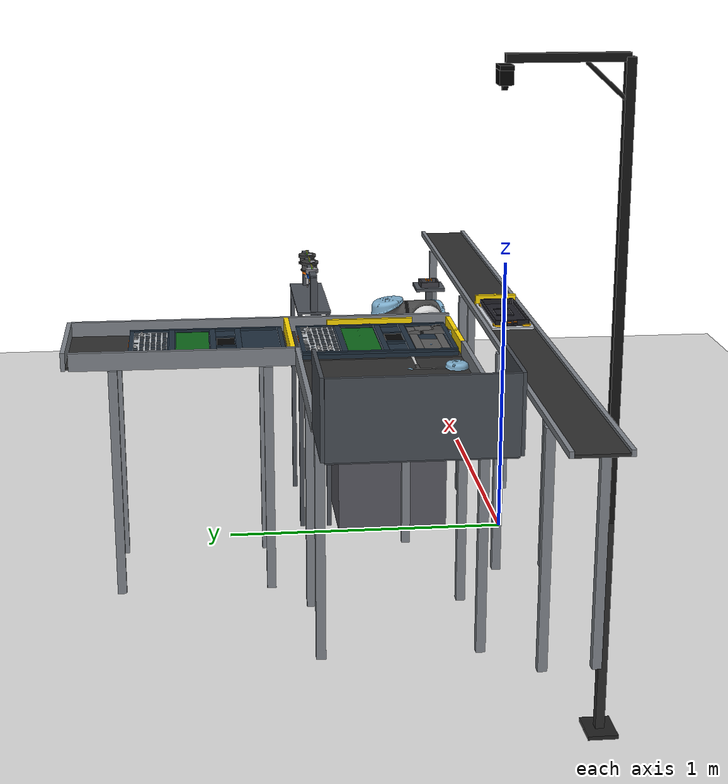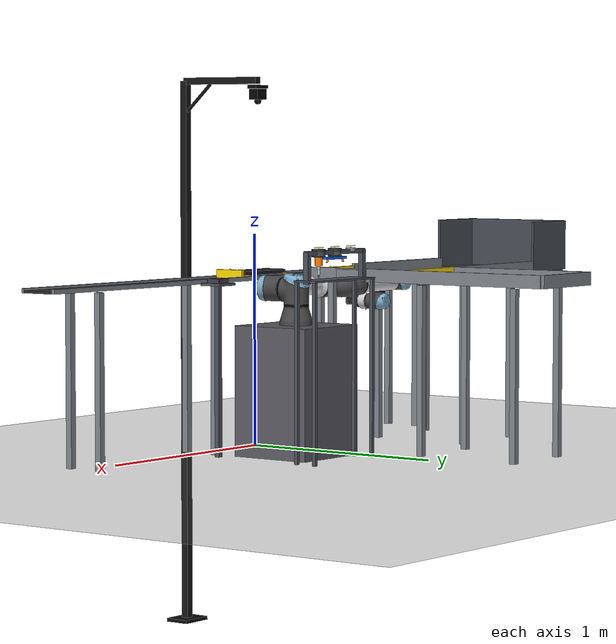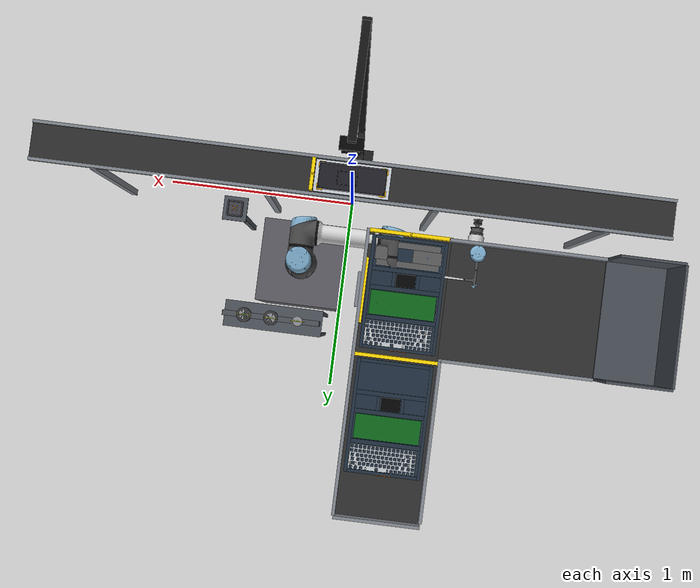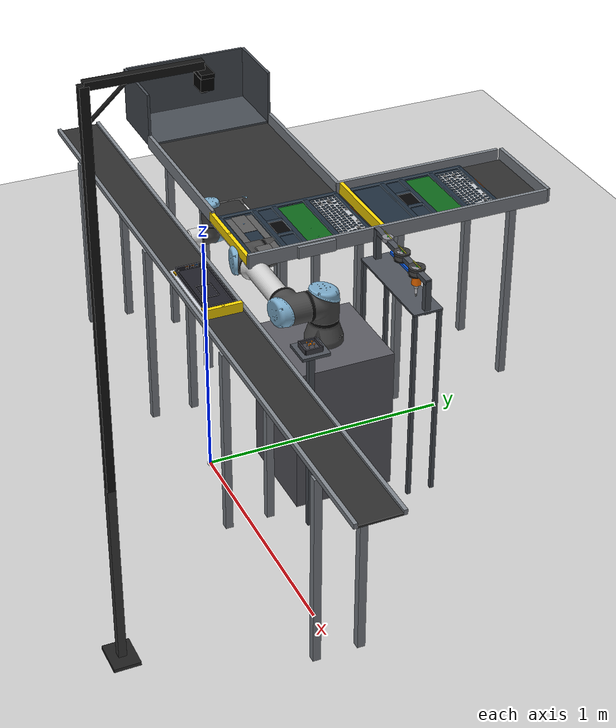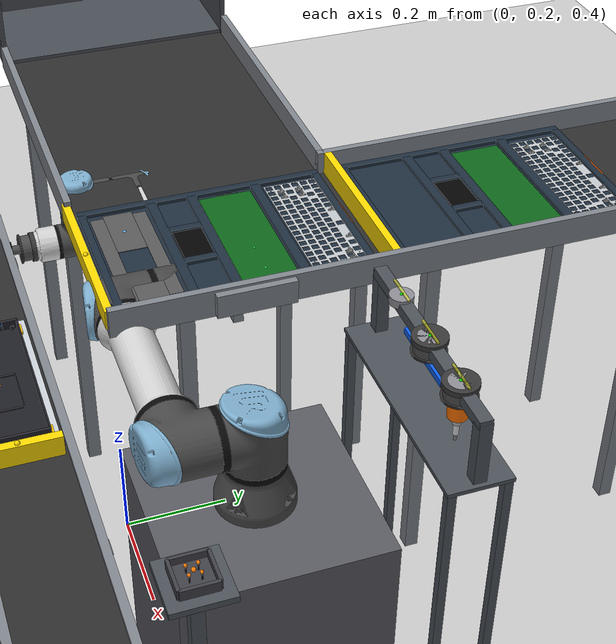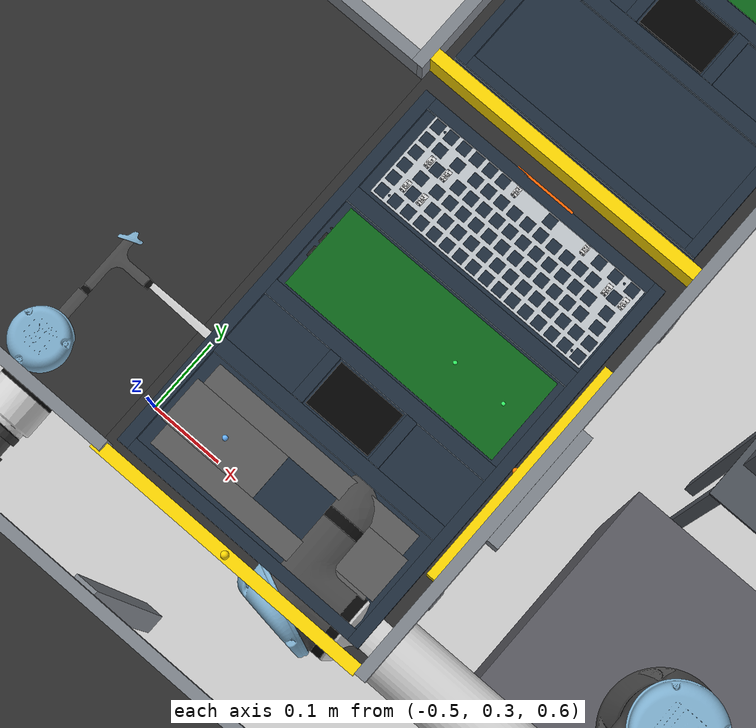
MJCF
<?xml version='1.0' encoding='utf-8'?>
<mujoco model="station1">
  <compiler angle="radian" meshdir="../robots/mujoco_menagerie/universal_robots_ur5e/assets" autolimits="true" />
  <option integrator="implicitfast" />
  <default>
    <default class="ur5e">
      <material specular="0.5" shininess="0.25" />
      <joint axis="0 1 0" range="-6.28319 6.28319" armature="0.1" />
      <general gaintype="fixed" biastype="affine" ctrlrange="-6.2831 6.2831" gainprm="2000" biasprm="0 -2000 -400" forcerange="-150 150" />
      <default class="size3">
        <default class="size3_limited">
          <joint range="-3.1415 3.1415" />
          <general ctrlrange="-3.1415 3.1415" />
        </default>
      </default>
      <default class="size1">
        <general gainprm="500" biasprm="0 -500 -100" forcerange="-28 28" />
      </default>
      <default class="visual">
        <geom type="mesh" contype="0" conaffinity="0" group="2" />
      </default>
      <default class="collision">
        <geom type="capsule" group="3" />
        <default class="eef_collision">
          <geom type="cylinder" />
        </default>
      </default>
      <site size="0.001" rgba="0.5 0.5 0.5 0.3" group="4" />
    </default>
  </default>
  <visual>
    <headlight diffuse="0.6 0.6 0.6" ambient="0.3 0.3 0.3" specular="0 0 0" />
    <rgba haze="0.15 0.25 0.35 1" />
    <global azimuth="120" elevation="-20" />
  </visual>
  <asset>
    <texture type="skybox" builtin="gradient" rgb1="0.3 0.5 0.7" rgb2="0 0 0" width="512" height="3072" />
    <texture name="grid" type="2d" builtin="checker" rgb1="0.3 0.3 0.3" rgb2="0.4 0.4 0.4" width="512" height="512" />
    <material name="floor_mat" texture="grid" texrepeat="5 5" reflectance="0.2" />
    <material name="conveyor_belt" rgba="0.18 0.18 0.18 1" />
    <material name="conveyor_rail" rgba="0.50 0.52 0.55 1" specular="0.4" shininess="0.3" />
    <material name="stopper_mat" rgba="1.0  0.85 0.0  1" />
    <material name="aluminum_pallet" rgba="0.80 0.82 0.85 1" specular="0.6" shininess="0.5" />
    <material name="fixture_stop" rgba="1.0  0.75 0.0  1" />
    <material name="abs_plastic" rgba="0.12 0.12 0.15 1" />
    <material name="tray_alu" rgba="0.12 0.18 0.24 1" specular="0.5" shininess="0.4" />
    <material name="tray_foam_epdm" rgba="0.12 0.12 0.14 1" specular="0.02" />
    <material name="tray_foam_batt" rgba="0.12 0.12 0.14 1" specular="0.02" />
    <material name="tray_foam_pcb" rgba="0.12 0.12 0.14 1" specular="0.02" />
    <material name="tray_foam_plate" rgba="0.12 0.12 0.14 1" specular="0.02" />
    <material name="tray_id" rgba="1.0  0.40 0.0  1" />
    <material name="stack_mat" rgba="0.28 0.30 0.33 1" />
    <material name="mat_epdm" rgba="0.35 0.35 0.35 1" specular="0.02" shininess="0.02" />
    <material name="mat_lipo" rgba="0.01 0.01 0.012 1" specular="0.25" shininess="0.25" />
    <material name="mat_connector" rgba="0.90 0.90 0.92 1" specular="0.9" shininess="0.8" />
    <material name="mat_fr4" rgba="0.05 0.40 0.10 1" specular="0.3" shininess="0.4" />
    <material name="mat_conn_dark" rgba="0.12 0.12 0.12 1" specular="0.5" shininess="0.6" />
    <material name="mat_alu_silver" rgba="0.95 0.10 0.10 1" specular="0.4" shininess="0.3" />
    <material name="mat_dock" rgba="0.30 0.32 0.35 1" />
    <material name="mat_cup" rgba="0.55 0.55 0.58 1" />
    <material name="mat_screw_box" rgba="0.25 0.25 0.28 1" />
    <material name="mat_screw" rgba="0.005 0.005 0.006 1" specular="0.35" shininess="0.35" />
    <material name="qc_camera_mat" rgba="0.04 0.04 0.045 1" specular="0.3" shininess="0.4" />
    <material name="qc_lens_mat" rgba="0.02 0.02 0.025 1" specular="0.8" shininess="0.8" />
    <material name="stab_white" rgba="0.86 0.86 0.86 1" specular="0.25" shininess="0.20" />
    <material name="stab_wire" rgba="0.70 0.70 0.72 1" specular="0.7" shininess="0.7" />
    <material class="ur5e" name="black" rgba="0.033 0.033 0.033 1" />
    <material class="ur5e" name="jointgray" rgba="0.278 0.278 0.278 1" />
    <material class="ur5e" name="linkgray" rgba="0.82  0.82  0.82  1" />
    <material class="ur5e" name="urblue" rgba="0.49  0.678 0.8   1" />
    <mesh file="base_0.obj" />
    <mesh file="base_1.obj" />
    <mesh file="shoulder_0.obj" />
    <mesh file="shoulder_1.obj" />
    <mesh file="shoulder_2.obj" />
    <mesh file="upperarm_0.obj" />
    <mesh file="upperarm_1.obj" />
    <mesh file="upperarm_2.obj" />
    <mesh file="upperarm_3.obj" />
    <mesh file="forearm_0.obj" />
    <mesh file="forearm_1.obj" />
    <mesh file="forearm_2.obj" />
    <mesh file="forearm_3.obj" />
    <mesh file="wrist1_0.obj" />
    <mesh file="wrist1_1.obj" />
    <mesh file="wrist1_2.obj" />
    <mesh file="wrist2_0.obj" />
    <mesh file="wrist2_1.obj" />
    <mesh file="wrist2_2.obj" />
    <mesh file="wrist3.obj" />
    <mesh name="aluminum_plate_mesh" file="aluminum_plate.stl" scale="0.001 0.001 0.001" />
    <mesh name="stabilizer_mesh" file="Stabilizer_Decimated.stl" scale="0.001 0.001 0.001" refpos="-23.958 0.000 -1.712" refquat="0.7071 -0.7071 0 0" />
  </asset>
  <worldbody>
    <light name="main_light" pos="0 0.5 4" dir="0 -0.1 -1" directional="true" />
    <light name="fill_light" pos="1 -0.2 3" dir="-0.3 0.2 -1" directional="true" diffuse="0.4 0.4 0.4" />
    <light name="spot" mode="targetbodycom" target="wrist_2_link" pos="0.2 0.4 3" />
    <geom name="floor" type="plane" size="5 5 0.05" material="floor_mat" />
    <body name="axes" pos="0 0 0">
      <geom type="cylinder" size="0.003 0.150" pos="0.150 0 0.003" euler="0 1.5708 0" rgba="1 0 0 1" contype="0" conaffinity="0" />
      <geom type="cylinder" size="0.003 0.150" pos="0 0.150 0.003" euler="1.5708 0 0" rgba="0 0.8 0 1" contype="0" conaffinity="0" />
      <geom type="cylinder" size="0.003 0.150" pos="0 0 0.150" rgba="0 0 1 1" contype="0" conaffinity="0" />
      <geom type="sphere" size="0.012" pos="0 0 0" rgba="1 1 1 1" contype="0" conaffinity="0" />
    </body>
    <body name="cdlr_main" pos="0 0 0">
      <geom name="cdlr_belt" type="box" size="1.500 0.080 0.005" pos="0 0 0.795" material="conveyor_belt" contype="1" conaffinity="1" />
      <geom name="cdlr_rail_f" type="box" size="1.500 0.0075 0.010" pos="0 -0.0875 0.8" material="conveyor_rail" contype="1" conaffinity="1" />
      <geom name="cdlr_rail_r" type="box" size="1.500 0.0075 0.010" pos="0  0.0875 0.8" material="conveyor_rail" contype="1" conaffinity="1" />
      <geom name="cl1f" type="box" size="0.015 0.015 0.392" pos="-1.200 -0.085 0.392" material="conveyor_rail" />
      <geom name="cl1r" type="box" size="0.015 0.015 0.392" pos="-1.200  0.085 0.392" material="conveyor_rail" />
      <geom name="cl2f" type="box" size="0.015 0.015 0.392" pos="-0.400 -0.085 0.392" material="conveyor_rail" />
      <geom name="cl2r" type="box" size="0.015 0.015 0.392" pos="-0.400  0.085 0.392" material="conveyor_rail" />
      <geom name="cl3f" type="box" size="0.015 0.015 0.392" pos=" 0.400 -0.085 0.392" material="conveyor_rail" />
      <geom name="cl3r" type="box" size="0.015 0.015 0.392" pos=" 0.400  0.085 0.392" material="conveyor_rail" />
      <geom name="cl4f" type="box" size="0.015 0.015 0.392" pos=" 1.200 -0.085 0.392" material="conveyor_rail" />
      <geom name="cl4r" type="box" size="0.015 0.015 0.392" pos=" 1.200  0.085 0.392" material="conveyor_rail" />
      <geom name="cdlr_stop" type="box" size="0.008 0.075 0.020" pos="0.185 0 0.820" material="stopper_mat" contype="1" conaffinity="1" />
      <site name="s_cdlr_stop" type="sphere" size="0.005" pos="0.185 0 0.840" rgba="1 0.85 0 1" />
    </body>
    <body name="pallet_base" pos="0 0 0.810" euler="0 0 3.1416">
      <geom name="pallet_plate" type="box" size="0.175 0.075 0.004" pos="0 0 -0.004" material="aluminum_pallet" mass="1.5" contype="1" conaffinity="1" />
      <geom name="stop_FL_x" type="box" size="0.0125 0.0025 0.003" pos="-0.1439 -0.0637  0.003" material="fixture_stop" mass="0.02" />
      <geom name="stop_FL_y" type="box" size="0.0025 0.0125 0.003" pos="-0.1589 -0.04865 0.003" material="fixture_stop" mass="0.02" />
      <geom name="stop_FR_x" type="box" size="0.0125 0.0025 0.003" pos=" 0.1439 -0.0637  0.003" material="fixture_stop" mass="0.02" />
      <geom name="stop_FR_y" type="box" size="0.0025 0.0125 0.003" pos=" 0.1589 -0.04865 0.003" material="fixture_stop" mass="0.02" />
      <geom name="stop_RL_x" type="box" size="0.0125 0.0025 0.003" pos="-0.1439  0.0637  0.003" material="fixture_stop" mass="0.02" />
      <geom name="stop_RL_y" type="box" size="0.0025 0.0125 0.003" pos="-0.1589  0.04865 0.003" material="fixture_stop" mass="0.02" />
      <geom name="stop_RR_x" type="box" size="0.0125 0.0025 0.003" pos=" 0.1439  0.0637  0.003" material="fixture_stop" mass="0.02" />
      <geom name="stop_RR_y" type="box" size="0.0025 0.0125 0.003" pos=" 0.1589  0.04865 0.003" material="fixture_stop" mass="0.02" />
      <site name="s_pallet_ctr" type="sphere" size="0.004" pos="0 0 0" rgba="1 0.8 0 0.8" />
    </body>
    <body name="s1_bottom_case" pos="0 0 0.821" euler="0 0 0">
      <inertial pos="0 0 0" mass="0.085" diaginertia="3.2e-5 2.4e-4 2.5e-4" />
      <geom name="s1_floor" type="box" size="0.1564 0.06115 0.0015" pos="0 0 -0.0095" material="abs_plastic" density="1050" friction="1.0 0.005 0.0001" condim="4" priority="1" />
      <geom name="s1_wl_A" type="box" size="0.0015 0.01433 0.0095" pos="-0.1549  0.04682  0.0015" material="abs_plastic" density="1050" friction="1.0 0.005 0.0001" condim="4" priority="1" />
      <geom name="s1_wl_ub" type="box" size="0.0015 0.0045  0.0045" pos="-0.1549  0.028   -0.0035" material="abs_plastic" density="1050" friction="1.0 0.005 0.0001" condim="4" priority="1" />
      <geom name="s1_wl_ua" type="box" size="0.0015 0.0045  0.003" pos="-0.1549  0.028    0.008" material="abs_plastic" density="1050" friction="1.0 0.005 0.0001" condim="4" priority="1" />
      <geom name="s1_wl_B" type="box" size="0.0015 0.003   0.0095" pos="-0.1549  0.0205   0.0015" material="abs_plastic" density="1050" friction="1.0 0.005 0.0001" condim="4" priority="1" />
      <geom name="s1_wl_pb" type="box" size="0.0015 0.007   0.004" pos="-0.1549  0.0105  -0.004" material="abs_plastic" density="1050" friction="1.0 0.005 0.0001" condim="4" priority="1" />
      <geom name="s1_wl_pa" type="box" size="0.0015 0.007   0.0025" pos="-0.1549  0.0105   0.0085" material="abs_plastic" density="1050" friction="1.0 0.005 0.0001" condim="4" priority="1" />
      <geom name="s1_wl_C" type="box" size="0.0015 0.005   0.0095" pos="-0.1549 -0.0005   0.0015" material="abs_plastic" density="1050" friction="1.0 0.005 0.0001" condim="4" priority="1" />
      <geom name="s1_wl_ob" type="box" size="0.0015 0.007   0.004" pos="-0.1549 -0.0095  -0.004" material="abs_plastic" density="1050" friction="1.0 0.005 0.0001" condim="4" priority="1" />
      <geom name="s1_wl_oa" type="box" size="0.0015 0.007   0.0025" pos="-0.1549 -0.0095   0.0085" material="abs_plastic" density="1050" friction="1.0 0.005 0.0001" condim="4" priority="1" />
      <geom name="s1_wl_D" type="box" size="0.0015 0.02233 0.0095" pos="-0.1549 -0.03883  0.0015" material="abs_plastic" density="1050" friction="1.0 0.005 0.0001" condim="4" priority="1" />
      <site name="s1_usbc" type="box" size="0.001 0.0045 0.002" pos="-0.1565  0.028   0.003" rgba="0 0.5 1 0.9" />
      <site name="s1_pwr" type="box" size="0.001 0.007  0.002" pos="-0.1565  0.0105  0.003" rgba="1 0.5 0 0.9" />
      <site name="s1_os" type="box" size="0.001 0.007  0.002" pos="-0.1565 -0.0095  0.003" rgba="1 0.5 0 0.9" />
      <geom name="s1_wr" type="box" size="0.0015 0.06115 0.0095" pos=" 0.1549  0       0.0015" material="abs_plastic" density="1050" friction="1.0 0.005 0.0001" condim="4" priority="1" />
      <geom name="s1_wrear" type="box" size="0.1564 0.0015  0.0095" pos="0  0.05965 0.0015" material="abs_plastic" density="1050" friction="1.0 0.005 0.0001" condim="4" priority="1" />
      <geom name="s1_wfrt" type="box" size="0.1564 0.0015  0.0095" pos="0 -0.05965 0.0015" material="abs_plastic" density="1050" friction="1.0 0.005 0.0001" condim="4" priority="1" />
      <geom name="s1_brl" type="box" size="0.045  0.00075 0.002" pos=" 0.025  -0.03075 -0.006" material="abs_plastic" density="1050" friction="1.0 0.005 0.0001" condim="4" priority="1" />
      <geom name="s1_brr" type="box" size="0.045  0.00075 0.002" pos=" 0.025   0.03075 -0.006" material="abs_plastic" density="1050" friction="1.0 0.005 0.0001" condim="4" priority="1" />
      <geom name="s1_brfl" type="box" size="0.00075 0.0125 0.002" pos="-0.02025 -0.0175  -0.006" material="abs_plastic" density="1050" friction="1.0 0.005 0.0001" condim="4" priority="1" />
      <geom name="s1_brfr" type="box" size="0.00075 0.0125 0.002" pos="-0.02025  0.0175  -0.006" material="abs_plastic" density="1050" friction="1.0 0.005 0.0001" condim="4" priority="1" />
      <geom name="s1_brrr" type="box" size="0.00075 0.030  0.002" pos=" 0.07025  0       -0.006" material="abs_plastic" density="1050" friction="1.0 0.005 0.0001" condim="4" priority="1" />
      <geom name="s1_boss_FL" type="cylinder" size="0.003 0.004" pos="-0.1515 -0.0495 -0.004" material="abs_plastic" density="1050" friction="1.0 0.005 0.0001" condim="4" priority="1" />
      <geom name="s1_boss_FR" type="cylinder" size="0.003 0.004" pos=" 0.1545 -0.0495 -0.004" material="abs_plastic" density="1050" friction="1.0 0.005 0.0001" condim="4" priority="1" />
      <geom name="s1_boss_RL" type="cylinder" size="0.003 0.004" pos="-0.1515  0.0495 -0.004" material="abs_plastic" density="1050" friction="1.0 0.005 0.0001" condim="4" priority="1" />
      <geom name="s1_boss_RR" type="cylinder" size="0.003 0.004" pos=" 0.1545  0.0495 -0.004" material="abs_plastic" density="1050" friction="1.0 0.005 0.0001" condim="4" priority="1" />
      <site name="s1_boss_FL_s" type="cylinder" size="0.003 0.001" pos="-0.1515 -0.0495 -0.0085" rgba="0.8 0.2 0.2 1" />
      <site name="s1_boss_FR_s" type="cylinder" size="0.003 0.001" pos=" 0.1545 -0.0495 -0.0085" rgba="0.8 0.2 0.2 1" />
      <site name="s1_boss_RL_s" type="cylinder" size="0.003 0.001" pos="-0.1515  0.0495 -0.0085" rgba="0.8 0.2 0.2 1" />
      <site name="s1_boss_RR_s" type="cylinder" size="0.003 0.001" pos=" 0.1545  0.0495 -0.0085" rgba="0.8 0.2 0.2 1" />
      <site name="s1_case_top" type="sphere" size="0.002" pos="0 0 0.011" rgba="0 0.6 0.8 0.4" />
    </body>
    <body name="robot_raiser" pos="0.200 0.400 0">
      <geom name="raiser" type="box" size="0.200 0.200 0.300" pos="0 0 0.300" rgba="0.35 0.35 0.38 1" contype="1" conaffinity="1" mass="50.0" />
    </body>
    <body name="ur5e_mount" pos="0.200 0.400 0.600" euler="0 0 3.1416">
      <body name="base" childclass="ur5e">
        <inertial mass="4.0" pos="0 0 0" diaginertia="0.00443333156 0.00443333156 0.0072" />
        <geom mesh="base_0" material="black" class="visual" />
        <geom mesh="base_1" material="jointgray" class="visual" />
        <body name="shoulder_link" pos="0 0 0.163">
          <inertial mass="3.7" pos="0 0 0" diaginertia="0.0102675 0.0102675 0.00666" />
          <joint name="shoulder_pan_joint" class="size3" axis="0 0 1" />
          <geom mesh="shoulder_0" material="urblue" class="visual" />
          <geom mesh="shoulder_1" material="black" class="visual" />
          <geom mesh="shoulder_2" material="jointgray" class="visual" />
          <geom class="collision" size="0.06 0.06" pos="0 0 -0.04" />
          <body name="upper_arm_link" pos="0 0.138 0" quat="1 0 1 0">
            <inertial mass="8.393" pos="0 0 0.2125" diaginertia="0.133886 0.133886 0.0151074" />
            <joint name="shoulder_lift_joint" class="size3" />
            <geom mesh="upperarm_0" material="linkgray" class="visual" />
            <geom mesh="upperarm_1" material="black" class="visual" />
            <geom mesh="upperarm_2" material="jointgray" class="visual" />
            <geom mesh="upperarm_3" material="urblue" class="visual" />
            <geom class="collision" pos="0 -0.04 0" quat="1 1 0 0" size="0.06 0.06" />
            <geom class="collision" size="0.05 0.2" pos="0 0 0.2" />
            <body name="forearm_link" pos="0 -0.131 0.425">
              <inertial mass="2.275" pos="0 0 0.196" diaginertia="0.0311796 0.0311796 0.004095" />
              <joint name="elbow_joint" class="size3_limited" />
              <geom mesh="forearm_0" material="urblue" class="visual" />
              <geom mesh="forearm_1" material="linkgray" class="visual" />
              <geom mesh="forearm_2" material="black" class="visual" />
              <geom mesh="forearm_3" material="jointgray" class="visual" />
              <geom class="collision" pos="0 0.08 0" quat="1 1 0 0" size="0.055 0.06" />
              <geom class="collision" size="0.038 0.19" pos="0 0 0.2" />
              <body name="wrist_1_link" pos="0 0 0.392" quat="1 0 1 0">
                <inertial mass="1.219" pos="0 0.127 0" diaginertia="0.0025599 0.0025599 0.0021942" />
                <joint name="wrist_1_joint" class="size1" />
                <geom mesh="wrist1_0" material="black" class="visual" />
                <geom mesh="wrist1_1" material="urblue" class="visual" />
                <geom mesh="wrist1_2" material="jointgray" class="visual" />
                <geom class="collision" pos="0 0.05 0" quat="1 1 0 0" size="0.04 0.07" />
                <body name="wrist_2_link" pos="0 0.127 0">
                  <inertial mass="1.219" pos="0 0 0.1" diaginertia="0.0025599 0.0025599 0.0021942" />
                  <joint name="wrist_2_joint" axis="0 0 1" class="size1" />
                  <geom mesh="wrist2_0" material="black" class="visual" />
                  <geom mesh="wrist2_1" material="urblue" class="visual" />
                  <geom mesh="wrist2_2" material="jointgray" class="visual" />
                  <geom class="collision" size="0.04 0.06" pos="0 0 0.04" />
                  <geom class="collision" pos="0 0.02 0.1" quat="1 1 0 0" size="0.04 0.04" />
                  <body name="wrist_3_link" pos="0 0 0.1">
                    <inertial mass="0.1889" pos="0 0.0771683 0" quat="1 0 0 1" diaginertia="0.000132134 9.90863e-05 9.90863e-05" />
                    <joint name="wrist_3_joint" class="size1" />
                    <geom material="linkgray" mesh="wrist3" class="visual" />
                    <geom class="eef_collision" pos="0 0.08 0" quat="1 1 0 0" size="0.04 0.02" />
                    <site name="attachment_site" pos="0 0.1 0" quat="-1 1 0 0" />
                    <body name="gripper" pos="0 0.1 0">
                      <geom name="g_mount_flange" type="cylinder" size="0.032 0.005" pos="0 0.005 0" euler="1.5708 0 0" rgba="0.22 0.22 0.22 1" contype="0" conaffinity="0" mass="0.05" />
                      <geom name="g_base_body" type="cylinder" size="0.028 0.010" pos="0 0.020 0" euler="1.5708 0 0" rgba="0.30 0.30 0.30 1" contype="0" conaffinity="0" mass="0.10" />
                      <geom name="g_base_ring" type="cylinder" size="0.032 0.002" pos="0 0.032 0" euler="1.5708 0 0" rgba="0.18 0.18 0.18 1" contype="0" conaffinity="0" mass="0.02" />
                      <geom name="g_neck" type="cylinder" size="0.010 0.008" pos="0 0.042 0" euler="1.5708 0 0" rgba="0.30 0.30 0.30 1" contype="0" conaffinity="0" mass="0.02" />
                      <geom name="g_bellows" type="cylinder" size="0.020 0.006" pos="0 0.056 0" euler="1.5708 0 0" rgba="0.08 0.08 0.08 1" contype="0" conaffinity="0" mass="0.03" />
                      <geom name="g_bellows2" type="cylinder" size="0.018 0.004" pos="0 0.066 0" euler="1.5708 0 0" rgba="0.08 0.08 0.08 1" contype="0" conaffinity="0" mass="0.02" />
                      <geom name="g_cup_rim" type="cylinder" size="0.022 0.002" pos="0 0.072 0" euler="1.5708 0 0" rgba="0.05 0.05 0.05 1" contype="0" conaffinity="0" mass="0.01" />
                      <site name="gripper_tip" pos="0 0.074 0" size="0.003" rgba="1 1 0 0.8" />
                      <body name="pin_gripper" pos="0 0 0">
                        <geom name="pin_mount_flange" type="cylinder" size="0.032 0.005" pos="0 0.005 0" euler="1.5708 0 0" rgba="0.22 0.22 0.22 0" contype="0" conaffinity="0" mass="0.05" />
                        <geom name="pin_base_body" type="cylinder" size="0.028 0.010" pos="0 0.020 0" euler="1.5708 0 0" rgba="0.30 0.30 0.30 0" contype="0" conaffinity="0" mass="0.10" />
                        <geom name="pin_base_ring" type="cylinder" size="0.032 0.002" pos="0 0.032 0" euler="1.5708 0 0" rgba="0.18 0.18 0.18 0" contype="0" conaffinity="0" mass="0.02" />
                        <geom name="ilock_base_block" type="box" size="0.075 0.006 0.012" pos="0 0.042 0" rgba="0.05 0.38 0.95 0" contype="0" conaffinity="0" mass="0.20" />
                        <geom name="ilock_L_stem" type="box" size="0.001 0.006 0.0045" pos="-0.05715 0.054 0" rgba="0.95 0.75 0.10 0" contype="0" conaffinity="0" mass="0.006" />
                        <geom name="ilock_L_hook" type="box" size="0.0025 0.001 0.0045" pos="-0.06065 0.061 0" rgba="0.95 0.45 0.05 0" contype="0" conaffinity="0" mass="0.004" />
                        <geom name="ilock_R_stem" type="box" size="0.001 0.006 0.0045" pos=" 0.05715 0.054 0" rgba="0.95 0.75 0.10 0" contype="0" conaffinity="0" mass="0.006" />
                        <geom name="ilock_R_hook" type="box" size="0.0025 0.001 0.0045" pos=" 0.06065 0.061 0" rgba="0.95 0.45 0.05 0" contype="0" conaffinity="0" mass="0.004" />
                        <site name="pin_tip" pos="0 0.061 0" size="0.003" rgba="1 0.8 0 0" />
                        <site name="plate_lock_tcp" pos="0 0.068 0" size="0.004" rgba="0 1 1 0.8" />
                        <site name="pin_L_tip" pos="-0.05715 0.061 0" size="0.0025" rgba="1 1 0 0.8" />
                        <site name="pin_R_tip" pos=" 0.05715 0.061 0" size="0.0025" rgba="1 1 0 0.8" />
                        <site name="pin_L_hook_contact" pos="-0.06065 0.061 0" size="0.0025" rgba="1 0.2 0 0.8" />
                        <site name="pin_R_hook_contact" pos=" 0.06065 0.061 0" size="0.0025" rgba="1 0.2 0 0.8" />
                        <site name="plate_attach_marker" pos="0 0.068 0" size="0.004" rgba="0 1 1 0.8" />
                      </body>
                      <body name="screwdriver" pos="0 0 0">
                        <geom name="sd_flange" type="cylinder" size="0.030 0.005" pos="0 0.005 0" euler="1.5708 0 0" rgba="0.278 0.278 0.278 0" contype="0" conaffinity="0" />
                        <geom name="sd_spring" type="cylinder" size="0.008 0.008" pos="0 0.018 0" euler="1.5708 0 0" rgba="0.7 0.7 0.7 0" contype="0" conaffinity="0" />
                        <geom name="sd_body" type="cylinder" size="0.018 0.020" pos="0 0.046 0" euler="1.5708 0 0" rgba="1.0 0.45 0.0 0" contype="0" conaffinity="0" />
                        <geom name="sd_shaft" type="cylinder" size="0.005 0.012" pos="0 0.078 0" euler="1.5708 0 0" rgba="0.8 0.8 0.82 0" contype="0" conaffinity="0" />
                        <geom name="sd_bit" type="cylinder" size="0.003 0.006" pos="0 0.096 0" euler="1.5708 0 0" rgba="0.5 0.5 0.5 0" contype="0" conaffinity="0" />
                        <site name="screwdriver_tip" pos="0 0.102 0" size="0.003" rgba="0 0 0 0" />
                      </body>
                    </body>
                  </body>
                </body>
              </body>
            </body>
          </body>
        </body>
      </body>
    </body>
    <body name="feeder_vert" pos="-0.300 0.8737 0">
      <geom name="fv_belt" type="box" size="0.190 0.6562 0.005" pos="0 0 0.795" material="conveyor_belt" contype="1" conaffinity="1" />
      <geom name="fv_rail_l" type="box" size="0.0075 0.3750 0.030" pos="-0.1975 0.2713 0.820" material="conveyor_rail" contype="1" conaffinity="1" />
      <geom name="fv_rail_r" type="box" size="0.0075 0.6562 0.030" pos=" 0.1975 0 0.820" material="conveyor_rail" contype="1" conaffinity="1" />
      <geom name="fv_cap_top" type="box" size="0.1975 0.0075 0.030" pos="0  0.6637 0.820" material="conveyor_rail" contype="0" conaffinity="0" />
      <geom name="fvl1r" type="box" size="0.015 0.015 0.392" pos=" 0.180 -0.506 0.392" material="conveyor_rail" />
      <geom name="fvl2l" type="box" size="0.015 0.015 0.392" pos="-0.180  0.000 0.392" material="conveyor_rail" />
      <geom name="fvl2r" type="box" size="0.015 0.015 0.392" pos=" 0.180  0.000 0.392" material="conveyor_rail" />
      <geom name="fvl3l" type="box" size="0.015 0.015 0.392" pos="-0.180  0.506 0.392" material="conveyor_rail" />
      <geom name="fvl3r" type="box" size="0.015 0.015 0.392" pos=" 0.180  0.506 0.392" material="conveyor_rail" />
      <geom name="fv_stop_pick" type="box" size="0.190 0.008 0.020" pos="0 -0.6515 0.820" material="stopper_mat" contype="1" conaffinity="1" />
      <site name="s_stop_pick" type="sphere" size="0.005" pos="0 -0.6517 0.840" rgba="1 0.85 0 1" />
      <geom name="fv_stop_pre" type="box" size="0.190 0.008 0.030" pos="0 -0.0817 0.820" material="stopper_mat" contype="1" conaffinity="1" />
      <site name="s_stop_pre" type="sphere" size="0.005" pos="0 -0.0817 0.840" rgba="1 0.85 0 1" />
    </body>
    <body name="feeder_horiz" pos="-0.8475 0.500 0">
      <geom name="fh_belt" type="box" size="0.360 0.280 0.005" pos="0 0 0.795" material="conveyor_belt" contype="1" conaffinity="1" />
      <geom name="fh_rail_r" type="box" size="0.350 0.0075 0.030" pos="0  0.2775 0.820" material="conveyor_rail" contype="1" conaffinity="1" />
      <geom name="fh_rail_f" type="box" size="0.370 0.0075 0.030" pos="0 -0.275 0.820" material="conveyor_rail" contype="1" conaffinity="1" />
      <geom name="fhl1f" type="box" size="0.015 0.015 0.392" pos="-0.200 -0.250 0.392" material="conveyor_rail" />
      <geom name="fhl1r" type="box" size="0.015 0.015 0.392" pos="-0.200  0.250 0.392" material="conveyor_rail" />
      <geom name="fhl2f" type="box" size="0.015 0.015 0.392" pos=" 0.200 -0.250 0.392" material="conveyor_rail" />
      <geom name="fhl2r" type="box" size="0.015 0.015 0.392" pos=" 0.200  0.250 0.392" material="conveyor_rail" />
    </body>
    <body name="tray_stack" pos="-1.348 0.500 0.800">
      <geom name="ts_base" type="box" size="0.140 0.270 0.008" pos="0 0 0" material="stack_mat" contype="1" conaffinity="1" mass="5.0" />
      <geom name="ts_wall_l" type="box" size="0.006 0.270 0.120" pos="-0.146 0 0.120" material="stack_mat" contype="0" conaffinity="0" />
      <geom name="ts_wall_f" type="box" size="0.146 0.006 0.120" pos="0 -0.276 0.120" material="stack_mat" contype="0" conaffinity="0" />
      <geom name="ts_wall_b" type="box" size="0.146 0.006 0.120" pos="0  0.276 0.120" material="stack_mat" contype="0" conaffinity="0" />
    </body>
    <body name="kit_tray_pickzone" pos="-0.300 0.500 0.815">
      <freejoint name="jnt_tray_pz" />
      <inertial pos="0 0 -0.0075" mass="3.5" diaginertia="5.0e-2 1.2e-1 1.5e-1" />
      <geom name="pz_slab" type="box" size="0.175 0.260 0.0075" pos="0 0 -0.0075" material="tray_alu" contype="1" conaffinity="1" />
      <geom name="pz_wl" type="box" size="0.0075 0.260 0.004" pos="-0.1675 0 0.004" material="tray_alu" contype="0" conaffinity="0" />
      <geom name="pz_wr" type="box" size="0.0075 0.260 0.004" pos=" 0.1675 0 0.004" material="tray_alu" contype="0" conaffinity="0" />
      <geom name="pz_wb" type="box" size="0.1600 0.0075 0.004" pos="0 -0.2525 0.004" material="tray_alu" contype="0" conaffinity="0" />
      <geom name="pz_wt" type="box" size="0.1600 0.0075 0.004" pos="0  0.2525 0.004" material="tray_alu" contype="0" conaffinity="0" />
      <geom name="pz_div1" type="box" size="0.1600 0.010 0.004" pos="0 -0.10700 0.004" material="tray_alu" contype="0" conaffinity="0" />
      <geom name="pz_div2" type="box" size="0.1600 0.010 0.004" pos="0 -0.02100 0.004" material="tray_alu" contype="0" conaffinity="0" />
      <geom name="pz_div3" type="box" size="0.1600 0.010 0.004" pos="0  0.11700 0.004" material="tray_alu" contype="0" conaffinity="0" />
      <geom name="pz_bsl" type="box" size="0.0075 0.0330 0.004" pos="-0.0555 -0.06370 0.004" material="tray_alu" contype="0" conaffinity="0" />
      <geom name="pz_bsr" type="box" size="0.0075 0.0330 0.004" pos=" 0.0555 -0.06370 0.004" material="tray_alu" contype="0" conaffinity="0" />
      <geom name="pz_fl_epdm" type="box" size="0.1564 0.06415 0.0015" pos="0 -0.18085 -0.0065" material="tray_foam_epdm" contype="1" conaffinity="1" />
      <geom name="pz_fl_batt" type="box" size="0.0480 0.0330  0.0015" pos="0 -0.06370 -0.0065" material="tray_foam_batt" contype="1" conaffinity="1" />
      <geom name="pz_fl_pcb" type="box" size="0.1540 0.0590  0.0015" pos="0  0.04830 -0.0065" material="tray_foam_pcb" contype="1" conaffinity="1" />
      <geom name="pz_fl_plt" type="box" size="0.1554 0.06015 0.0015" pos="0  0.18745 -0.0065" material="tray_foam_plate" contype="1" conaffinity="1" />
      <geom name="pz_id" type="box" size="0.040 0.0015 0.002" pos="0 0.2600 0.006" material="tray_id" contype="0" conaffinity="0" />
      <site name="pz_pick_epdm" type="sphere" size="0.004" pos="0 -0.18085 -0.00425" rgba="0.5 0.6 1.0 0.9" />
      <site name="pz_pick_batt" type="sphere" size="0.004" pos="0 -0.06370 -0.002" rgba="0.9 0.9 0.3 0.9" />
      <site name="pz_pick_pcb" type="sphere" size="0.004" pos="0  0.04830 -0.0042" rgba="0.3 0.9 0.4 0.9" />
      <site name="pz_pick_plate" type="sphere" size="0.004" pos="0  0.18745 -0.00425" rgba="0.9 0.9 0.9 0.9" />
    </body>
    <body name="kit_tray_prestage" pos="-0.300 1.070 0.815">
      <freejoint name="jnt_tray_ps" />
      <inertial pos="0 0 -0.0075" mass="3.5" diaginertia="5.0e-2 1.2e-1 1.5e-1" />
      <geom name="ps_slab" type="box" size="0.175 0.260 0.0075" pos="0 0 -0.0075" material="tray_alu" contype="1" conaffinity="1" />
      <geom name="ps_wl" type="box" size="0.0075 0.260 0.004" pos="-0.1675 0 0.004" material="tray_alu" contype="0" conaffinity="0" />
      <geom name="ps_wr" type="box" size="0.0075 0.260 0.004" pos=" 0.1675 0 0.004" material="tray_alu" contype="0" conaffinity="0" />
      <geom name="ps_wb" type="box" size="0.1600 0.0075 0.004" pos="0 -0.2525 0.004" material="tray_alu" contype="0" conaffinity="0" />
      <geom name="ps_wt" type="box" size="0.1600 0.0075 0.004" pos="0  0.2525 0.004" material="tray_alu" contype="0" conaffinity="0" />
      <geom name="ps_div1" type="box" size="0.1600 0.010 0.004" pos="0 -0.10700 0.004" material="tray_alu" contype="0" conaffinity="0" />
      <geom name="ps_div2" type="box" size="0.1600 0.010 0.004" pos="0 -0.02100 0.004" material="tray_alu" contype="0" conaffinity="0" />
      <geom name="ps_div3" type="box" size="0.1600 0.010 0.004" pos="0  0.11700 0.004" material="tray_alu" contype="0" conaffinity="0" />
      <geom name="ps_bsl" type="box" size="0.0075 0.0330 0.004" pos="-0.0555 -0.06370 0.004" material="tray_alu" contype="0" conaffinity="0" />
      <geom name="ps_bsr" type="box" size="0.0075 0.0330 0.004" pos=" 0.0555 -0.06370 0.004" material="tray_alu" contype="0" conaffinity="0" />
      <geom name="ps_fl_epdm" type="box" size="0.1564 0.06415 0.0015" pos="0 -0.18085 -0.0065" material="tray_foam_epdm" contype="0" conaffinity="0" />
      <geom name="ps_fl_batt" type="box" size="0.0480 0.0330  0.0015" pos="0 -0.06370 -0.0065" material="tray_foam_batt" contype="0" conaffinity="0" />
      <geom name="ps_fl_pcb" type="box" size="0.1540 0.0590  0.0015" pos="0  0.04830 -0.0065" material="tray_foam_pcb" contype="0" conaffinity="0" />
      <geom name="ps_fl_plt" type="box" size="0.1554 0.06015 0.0015" pos="0  0.18745 -0.0065" material="tray_foam_plate" contype="0" conaffinity="0" />
      <geom name="ps_id" type="box" size="0.040 0.0015 0.002" pos="0  0.2600  0.006" material="tray_id" contype="0" conaffinity="0" />
    </body>
    <body name="ps_epdm" pos="-0.3000 0.88915 0.81075">
      <freejoint name="jnt_ps_epdm" />
      <inertial pos="0 0 0" mass="0.008" diaginertia="1.2e-5 3.8e-5 5.0e-5" />
      <geom name="ps_epdm_f" type="box" size="0.1454 0.01408 0.00075" pos="0 -0.04408 0.002" material="mat_epdm" density="200" friction="0.8 0.005 0.0001" condim="4" />
      <geom name="ps_epdm_r" type="box" size="0.1454 0.01408 0.00075" pos="0  0.04408 0.002" material="mat_epdm" density="200" friction="0.8 0.005 0.0001" condim="4" />
      <geom name="ps_epdm_l" type="box" size="0.06670 0.030 0.00075" pos="-0.08670 0 0.002" material="mat_epdm" density="200" friction="0.8 0.005 0.0001" condim="4" />
      <geom name="ps_epdm_g" type="box" size="0.04170 0.030 0.00075" pos=" 0.11170 0 0.002" material="mat_epdm" density="200" friction="0.8 0.005 0.0001" condim="4" />
    </body>
    <body name="ps_battery" pos="-0.3000 1.00630 0.81300">
      <freejoint name="jnt_ps_battery" />
      <inertial pos="0 0 0" mass="0.080" diaginertia="3.6e-5 1.6e-4 1.8e-4" />
      <geom name="ps_batt_body" type="box" size="0.045 0.030 0.004" pos="0 0 0.004" material="mat_lipo" density="2400" friction="0.6 0.005 0.0001" condim="4" />
    </body>
    <body name="ps_pcb" pos="-0.3000 1.11830 0.81200">
      <freejoint name="jnt_ps_pcb" />
      <inertial pos="0 0 0" mass="0.100" diaginertia="9.3e-5 8.1e-4 8.9e-4" />
      <geom name="ps_pcb_board" type="box" size="0.1510 0.0560 0.002" pos="0 0 0.002" material="mat_fr4" density="1850" friction="0.6 0.005 0.0001" condim="4" />
    </body>
    <body name="ps_plate" pos="-0.3000 1.25745 0.81375" quat="0 0 0 1">
      <freejoint name="jnt_ps_plate" />
      <inertial pos="0 0 0.00075" mass="0.138" diaginertia="1.4e-4 1.3e-3 1.4e-3" />
      <geom name="ps_alu_vis" type="mesh" mesh="aluminum_plate_mesh" pos="-0.002361 0.000056 0.000747" rgba="0.76 0.78 0.80 1" density="2700" friction="0.4 0.005 0.0001" condim="4" />
      <body name="ps_stab_space_L" pos="-0.07693 -0.05113 -0.00550">
        <geom name="ps_stab_space_L_mesh" type="mesh" mesh="stabilizer_mesh" pos="-0.047852 0.0017 0.00650" material="stab_white" contype="0" conaffinity="0" />
      </body>
      <body name="ps_stab_space_R" pos="0.02307 -0.05113 -0.00550">
        <geom name="ps_stab_space_R_mesh" type="mesh" mesh="stabilizer_mesh" pos="-0.047852 0.0017 0.00650" material="stab_white" contype="0" conaffinity="0" />
      </body>
      <body name="ps_stab_lshift_L" pos="-0.14841 -0.03208 -0.00550">
        <geom name="ps_stab_lshift_L_mesh" type="mesh" mesh="stabilizer_mesh" pos="-0.047852 0.0017 0.00650" material="stab_white" contype="0" conaffinity="0" />
      </body>
      <body name="ps_stab_lshift_R" pos="-0.12453 -0.03208 -0.00550">
        <geom name="ps_stab_lshift_R_mesh" type="mesh" mesh="stabilizer_mesh" pos="-0.047852 0.0017 0.00650" material="stab_white" contype="0" conaffinity="0" />
      </body>
      <body name="ps_stab_enter_L" pos="0.09448 -0.01302 -0.00550">
        <geom name="ps_stab_enter_L_mesh" type="mesh" mesh="stabilizer_mesh" pos="-0.047852 0.0017 0.00650" material="stab_white" contype="0" conaffinity="0" />
      </body>
      <body name="ps_stab_enter_R" pos="0.11836 -0.01302 -0.00550">
        <geom name="ps_stab_enter_R_mesh" type="mesh" mesh="stabilizer_mesh" pos="-0.047852 0.0017 0.00650" material="stab_white" contype="0" conaffinity="0" />
      </body>
      <body name="ps_stab_bksp_L" pos="0.09686 0.02508 -0.00550">
        <geom name="ps_stab_bksp_L_mesh" type="mesh" mesh="stabilizer_mesh" pos="-0.047852 0.0017 0.00650" material="stab_white" contype="0" conaffinity="0" />
      </body>
      <body name="ps_stab_bksp_R" pos="0.12074 0.02508 -0.00550">
        <geom name="ps_stab_bksp_R_mesh" type="mesh" mesh="stabilizer_mesh" pos="-0.047852 0.0017 0.00650" material="stab_white" contype="0" conaffinity="0" />
      </body>
    </body>
         Tray world: (−0.200, 0.400, 0.815), pocket floor z=0.810
         EPDM local Y=−0.181 → world (−0.200, 0.21915, 0.81075)
         ══════════════════════════════════════════════════════════════════ --&gt;

    <body name="s1_epdm" pos="-0.3000 0.31915 0.81375">
      <freejoint name="jnt_epdm" />
      <inertial pos="0 0 0" mass="0.008" diaginertia="1.2e-5 3.8e-5 5.0e-5" />
      <geom name="epdm_front" type="box" size="0.1454 0.01408 0.00075" pos="0 -0.04408 0.002" material="mat_epdm" density="200" friction="0.8 0.005 0.0001" condim="4" />
      <geom name="epdm_rear" type="box" size="0.1454 0.01408 0.00075" pos="0  0.04408 0.002" material="mat_epdm" density="200" friction="0.8 0.005 0.0001" condim="4" />
      <geom name="epdm_left" type="box" size="0.06670 0.030 0.00075" pos="-0.08670 0 0.002" material="mat_epdm" density="200" friction="0.8 0.005 0.0001" condim="4" />
      <geom name="epdm_right" type="box" size="0.04170 0.030 0.00075" pos=" 0.11170 0 0.002" material="mat_epdm" density="200" friction="0.8 0.005 0.0001" condim="4" />
      <site name="s1_epdm_grasp" type="sphere" size="0.004" pos="-0.087 0 0.00075" rgba="0.4 0.7 1.0 0.9" />
    </body>
    <body name="s1_battery" pos="-0.3000 0.43630 0.81300">
      <freejoint name="jnt_battery" />
      <inertial pos="0 0 0" mass="0.080" diaginertia="3.6e-5 1.6e-4 1.8e-4" />
      <geom name="batt_body" type="box" size="0.045 0.030 0.004" pos="0 0 0.004" material="mat_lipo" density="2400" friction="0.6 0.005 0.0001" condim="4" />
      <geom name="batt_jst" type="box" size="0.001 0.004 0.002" pos="-0.046 0 -0.001" material="mat_connector" contype="0" conaffinity="0" />
      <site name="s1_battery_grasp" type="sphere" size="0.004" pos="0 0 0.003" rgba="1.0 0.9 0.2 0.9" />
      <site name="s1_jst_face" type="sphere" size="0.002" pos="-0.045 0 0" rgba="1 0.4 0 0.8" />
    </body>
    <body name="s1_pcb" pos="-0.3000 0.54830 0.81200">
      <freejoint name="jnt_pcb" />
      <inertial pos="0 0 0" mass="0.100" diaginertia="9.3e-5 8.1e-4 8.9e-4" />
      <geom name="pcb_board" type="box" size="0.1510 0.0560 0.002" pos="0 0 0.002" material="mat_fr4" density="1850" friction="0.6 0.005 0.0001" condim="4" />
      <geom name="pcb_usbc" type="box" size="0.0015 0.0045 0.002" pos="-0.1525  0.028  0.001" material="mat_conn_dark" contype="0" conaffinity="0" />
      <geom name="pcb_pwr" type="box" size="0.0015 0.007  0.003" pos="-0.1525  0.0105 0.002" material="mat_conn_dark" contype="0" conaffinity="0" />
      <geom name="pcb_os" type="box" size="0.0015 0.007  0.003" pos="-0.1525 -0.0095 0.002" material="mat_conn_dark" contype="0" conaffinity="0" />
      <site name="s1_pcb_gl" type="sphere" size="0.004" pos="0.05 0 0.0008" rgba="0.2 1.0 0.4 0.9" />
      <site name="s1_pcb_gr" type="sphere" size="0.004" pos="0.12 0 0.0008" rgba="0.2 1.0 0.4 0.9" />
    </body>
    <body name="s1_alu_plate" pos="-0.3000 0.68745 0.81775" quat="0 0 0 1">
      <freejoint name="jnt_alu_plate" />
      <inertial pos="0 0 0.00075" mass="0.138" diaginertia="1.4e-4 1.3e-3 1.4e-3" />
      <geom name="alu_vis" type="mesh" mesh="aluminum_plate_mesh" pos="-0.002361 0.000056 0.000747" rgba="0.76 0.78 0.80 1" />
      <site name="s1_alu_gl" type="sphere" size="0.004" pos="-0.06 0 0.0015" rgba="0 0 0 0" />
      <site name="s1_alu_gr" type="sphere" size="0.004" pos=" 0.06 0 0.0015" rgba="0 0 0 0" />
      <body name="stab_space_L" pos="-0.07693 -0.05113 -0.00550">
        <geom name="stab_space_L_mesh" type="mesh" mesh="stabilizer_mesh" pos="-0.047852 0.0017 0.00650" material="stab_white" contype="0" conaffinity="0" />
      </body>
      <body name="stab_space_R" pos="0.02307 -0.05113 -0.00550">
        <geom name="stab_space_R_mesh" type="mesh" mesh="stabilizer_mesh" pos="-0.047852 0.0017 0.00650" material="stab_white" contype="0" conaffinity="0" />
      </body>
      <body name="stab_lshift_L" pos="-0.14841 -0.03208 -0.00550">
        <geom name="stab_lshift_L_mesh" type="mesh" mesh="stabilizer_mesh" pos="-0.047852 0.0017 0.00650" material="stab_white" contype="0" conaffinity="0" />
      </body>
      <body name="stab_lshift_R" pos="-0.12453 -0.03208 -0.00550">
        <geom name="stab_lshift_R_mesh" type="mesh" mesh="stabilizer_mesh" pos="-0.047852 0.0017 0.00650" material="stab_white" contype="0" conaffinity="0" />
      </body>
      <body name="stab_enter_L" pos="0.09448 -0.01302 -0.00550">
        <geom name="stab_enter_L_mesh" type="mesh" mesh="stabilizer_mesh" pos="-0.047852 0.0017 0.00650" material="stab_white" contype="0" conaffinity="0" />
      </body>
      <body name="stab_enter_R" pos="0.11836 -0.01302 -0.00550">
        <geom name="stab_enter_R_mesh" type="mesh" mesh="stabilizer_mesh" pos="-0.047852 0.0017 0.00650" material="stab_white" contype="0" conaffinity="0" />
      </body>
      <body name="stab_bksp_L" pos="0.09686 0.02508 -0.00550">
        <geom name="stab_bksp_L_mesh" type="mesh" mesh="stabilizer_mesh" pos="-0.047852 0.0017 0.00650" material="stab_white" contype="0" conaffinity="0" />
      </body>
      <body name="stab_bksp_R" pos="0.12074 0.02508 -0.00550">
        <geom name="stab_bksp_R_mesh" type="mesh" mesh="stabilizer_mesh" pos="-0.047852 0.0017 0.00650" material="stab_white" contype="0" conaffinity="0" />
      </body>
    </body>
    <body name="tool_dock" pos="0.280 0.680 0.870">
      <geom name="dock_base" type="box" size="0.225 0.060 0.004" pos="0 0 -0.05" material="mat_dock" contype="1" conaffinity="1" mass="2.0" />
      <geom name="dock_post_1" type="box" size="0.012 0.012 0.07" pos="-0.205 0 0.009" material="mat_dock" contype="1" conaffinity="1" mass="0.5" />
      <geom name="dock_post_2" type="box" size="0.012 0.012 0.07" pos="0.205 0 0.009" material="mat_dock" contype="1" conaffinity="1" mass="0.5" />
      <geom name="dock_arm" type="box" size="0.215 0.012 0.010" pos="0 0 0.074" material="mat_dock" contype="1" conaffinity="1" mass="0.3" />
      <geom name="dock_leg_fl" type="box" size="0.008 0.008 0.408" pos="-0.215 -0.050 -0.46" material="mat_dock" contype="1" conaffinity="1" />
      <geom name="dock_leg_fr" type="box" size="0.008 0.008 0.408" pos=" 0.215 -0.050 -0.46" material="mat_dock" contype="1" conaffinity="1" />
      <geom name="dock_leg_rl" type="box" size="0.008 0.008 0.408" pos="-0.215  0.050 -0.46" material="mat_dock" contype="1" conaffinity="1" />
      <geom name="dock_leg_rr" type="box" size="0.008 0.008 0.408" pos=" 0.215  0.050 -0.46" material="mat_dock" contype="1" conaffinity="1" />
      <geom name="cup_vac" type="cylinder" size="0.022 0.008" pos="-0.120 0 0.082" material="mat_cup" contype="0" conaffinity="0" />
      <site name="dock_vac_W2" type="sphere" size="0.003" pos="-0.120 0 0.090" rgba="0 1 0 0.9" />
      <site name="dock_vac_flat_axis" type="box" size="0.032 0.002 0.002" pos="-0.120 0 0.098" rgba="1 1 0 0.45" />
      <geom name="cup_pin" type="cylinder" size="0.022 0.008" pos="0 0 0.082" material="mat_cup" contype="0" conaffinity="0" />
      <site name="dock_pin_W2" type="sphere" size="0.003" pos="0 0 0.090" rgba="0 1 0 0.9" />
      <site name="dock_pin_flat_axis" type="box" size="0.032 0.002 0.002" pos="0 0 0.098" rgba="1 1 0 0.45" />
      <geom name="cup_sd" type="cylinder" size="0.022 0.008" pos="0.120 0 0.082" material="mat_cup" contype="0" conaffinity="0" />
      <site name="dock_sd_W2" type="sphere" size="0.003" pos="0.120 0 0.090" rgba="0 1 0 0.9" />
      <site name="dock_sd_flat_axis" type="box" size="0.032 0.002 0.002" pos="0.120 0 0.098" rgba="1 1 0 0.45" />
      <body name="dock_vac_vis" pos="-0.120 0 0.090" euler="3.1416 0 0">
        <geom type="cylinder" size="0.032 0.005" pos="0 0 0.005" rgba="0.22 0.22 0.22 0" contype="0" conaffinity="0" />
        <geom type="cylinder" size="0.028 0.010" pos="0 0 0.020" rgba="0.30 0.30 0.30 0" contype="0" conaffinity="0" />
        <geom type="cylinder" size="0.032 0.002" pos="0 0 0.032" rgba="0.18 0.18 0.18 0" contype="0" conaffinity="0" />
        <geom type="cylinder" size="0.010 0.008" pos="0 0 0.042" rgba="0.30 0.30 0.30 0" contype="0" conaffinity="0" />
        <geom type="cylinder" size="0.020 0.006" pos="0 0 0.056" rgba="0.08 0.08 0.08 0" contype="0" conaffinity="0" />
        <geom type="cylinder" size="0.018 0.004" pos="0 0 0.066" rgba="0.08 0.08 0.08 0" contype="0" conaffinity="0" />
        <geom type="cylinder" size="0.022 0.002" pos="0 0 0.072" rgba="0.05 0.05 0.05 0" contype="0" conaffinity="0" />
      </body>
      <body name="dock_pin_vis" pos="0 0.000 0.090" euler="3.1416 0 0">
        <geom type="cylinder" size="0.032 0.005" pos="0 0 0.005" rgba="0.22 0.22 0.22 1" contype="0" conaffinity="0" />
        <geom type="cylinder" size="0.028 0.010" pos="0 0 0.020" rgba="0.30 0.30 0.30 1" contype="0" conaffinity="0" />
        <geom type="cylinder" size="0.032 0.002" pos="0 0 0.032" rgba="0.18 0.18 0.18 1" contype="0" conaffinity="0" />
        <geom type="box" size="0.075 0.012 0.006" pos="0 0 0.042" rgba="0.05 0.38 0.95 1" contype="0" conaffinity="0" />
        <geom type="box" size="0.001 0.0045 0.006" pos="-0.05715 0 0.054" rgba="0.95 0.75 0.10 1" contype="0" conaffinity="0" />
        <geom type="box" size="0.0025 0.0045 0.001" pos="-0.06065 0 0.061" rgba="0.95 0.45 0.05 1" contype="0" conaffinity="0" />
        <geom type="box" size="0.001 0.0045 0.006" pos=" 0.05715 0 0.054" rgba="0.95 0.75 0.10 1" contype="0" conaffinity="0" />
        <geom type="box" size="0.0025 0.0045 0.001" pos=" 0.06065 0 0.061" rgba="0.95 0.45 0.05 1" contype="0" conaffinity="0" />
      </body>
      <body name="dock_sd_vis" pos="0.120 0 0.090" euler="3.1416 0 0">
        <geom type="cylinder" size="0.032 0.005" pos="0 0 0.005" rgba="0.22 0.22 0.22 1" contype="0" conaffinity="0" />
        <geom type="cylinder" size="0.028 0.010" pos="0 0 0.020" rgba="0.30 0.30 0.30 1" contype="0" conaffinity="0" />
        <geom type="cylinder" size="0.032 0.002" pos="0 0 0.032" rgba="0.18 0.18 0.18 1" contype="0" conaffinity="0" />
        <geom type="cylinder" size="0.018 0.020" pos="0 0 0.054" rgba="1.00 0.45 0.00 1" contype="0" conaffinity="0" />
        <geom type="cylinder" size="0.008 0.008" pos="0 0 0.082" rgba="0.70 0.70 0.70 1" contype="0" conaffinity="0" />
        <geom type="cylinder" size="0.005 0.012" pos="0 0 0.102" rgba="0.85 0.85 0.87 1" contype="0" conaffinity="0" />
        <geom type="cylinder" size="0.003 0.006" pos="0 0 0.120" rgba="0.50 0.50 0.50 1" contype="0" conaffinity="0" />
      </body>
    </body>
    <body name="screw_box" pos="0.520 0.200 0.800">
      <geom name="sbox_pedestal_top" type="box" size="0.055 0.055 0.006" pos="0 0 -0.006" material="mat_dock" contype="1" conaffinity="1" mass="1.0" />
      <geom name="sbox_pedestal_leg" type="box" size="0.012 0.012 0.390" pos="0 0 -0.402" material="mat_dock" contype="1" conaffinity="1" mass="2.0" />
      <geom name="sbox_floor" type="box" size="0.033 0.033 0.003" pos="0 0 0.003" material="mat_screw_box" contype="1" conaffinity="1" mass="0.2" />
      <geom name="sbox_wf" type="box" size="0.033 0.003 0.010" pos="0 -0.033 0.010" material="mat_screw_box" contype="0" conaffinity="0" />
      <geom name="sbox_wr" type="box" size="0.033 0.003 0.010" pos="0  0.033 0.010" material="mat_screw_box" contype="0" conaffinity="0" />
      <geom name="sbox_wl" type="box" size="0.003 0.033 0.010" pos="-0.033 0 0.010" material="mat_screw_box" contype="0" conaffinity="0" />
      <geom name="sbox_wrr" type="box" size="0.003 0.033 0.010" pos=" 0.033 0 0.010" material="mat_screw_box" contype="0" conaffinity="0" />
      <site name="screw_pick_site" type="sphere" size="0.004" pos="0 0 0.020" rgba="1 0.5 0 0.9" />
      <site name="screw_pick_FL" type="sphere" size="0.003" pos="-0.010 -0.010 0.022" rgba="1 0.5 0 0.9" />
      <site name="screw_pick_FR" type="sphere" size="0.003" pos=" 0.010 -0.010 0.022" rgba="1 0.5 0 0.9" />
      <site name="screw_pick_RL" type="sphere" size="0.003" pos="-0.010  0.010 0.022" rgba="1 0.5 0 0.9" />
      <site name="screw_pick_RR" type="sphere" size="0.003" pos=" 0.010  0.010 0.022" rgba="1 0.5 0 0.9" />
    </body>
    <body name="screw_FL" pos="0.510 0.190 0.806">
      <freejoint name="jnt_screw_FL" />
      <inertial pos="0 0 0.006" mass="0.0005" diaginertia="1e-9 1e-9 5e-10" />
      <geom name="sFL_s" type="cylinder" size="0.0014 0.005" pos="0 0 0.005" material="mat_screw" contype="0" conaffinity="0" />
      <geom name="sFL_h" type="cylinder" size="0.002 0.001" pos="0 0 0.011" material="mat_screw" contype="0" conaffinity="0" />
      <site name="sFL_tip" type="sphere" size="0.001" pos="0 0 0" rgba="1 0.2 0.2 0.9" />
      <site name="sFL_eng" type="sphere" size="0.001" pos="0 0 0.016" rgba="0 0.6 1.0 0.9" />
    </body>
    <body name="screw_FR" pos="0.530 0.190 0.806">
      <freejoint name="jnt_screw_FR" />
      <inertial pos="0 0 0.006" mass="0.0005" diaginertia="1e-9 1e-9 5e-10" />
      <geom name="sFR_s" type="cylinder" size="0.0014 0.005" pos="0 0 0.005" material="mat_screw" contype="0" conaffinity="0" />
      <geom name="sFR_h" type="cylinder" size="0.002 0.001" pos="0 0 0.011" material="mat_screw" contype="0" conaffinity="0" />
      <site name="sFR_tip" type="sphere" size="0.001" pos="0 0 0" rgba="1 0.2 0.2 0.9" />
      <site name="sFR_eng" type="sphere" size="0.001" pos="0 0 0.016" rgba="0 0.6 1.0 0.9" />
    </body>
    <body name="screw_RL" pos="0.510 0.210 0.806">
      <freejoint name="jnt_screw_RL" />
      <inertial pos="0 0 0.006" mass="0.0005" diaginertia="1e-9 1e-9 5e-10" />
      <geom name="sRL_s" type="cylinder" size="0.0014 0.005" pos="0 0 0.005" material="mat_screw" contype="0" conaffinity="0" />
      <geom name="sRL_h" type="cylinder" size="0.0020 0.001" pos="0 0 0.011" material="mat_screw" contype="0" conaffinity="0" />
      <site name="sRL_tip" type="sphere" size="0.001" pos="0 0 0" rgba="1 0.2 0.2 0.9" />
      <site name="sRL_eng" type="sphere" size="0.001" pos="0 0 0.016" rgba="0 0.6 1.0 0.9" />
    </body>
    <body name="screw_RR" pos="0.530 0.210 0.806">
      <freejoint name="jnt_screw_RR" />
      <inertial pos="0 0 0.006" mass="0.0005" diaginertia="1e-9 1e-9 5e-10" />
      <geom name="sRR_s" type="cylinder" size="0.0014 0.005" pos="0 0 0.005" material="mat_screw" contype="0" conaffinity="0" />
      <geom name="sRR_h" type="cylinder" size="0.002 0.001" pos="0 0 0.011" material="mat_screw" contype="0" conaffinity="0" />
      <site name="sRR_tip" type="sphere" size="0.001" pos="0 0 0" rgba="1 0.2 0.2 0.9" />
      <site name="sRR_eng" type="sphere" size="0.001" pos="0 0 0.016" rgba="0 0.6 1.0 0.9" />
    </body>
    <body name="slider_mount" pos="-0.105 0.500 0.820">
      <geom name="slider_bracket" type="box" size="0.010 0.080 0.025" pos="0.015 0 0" material="conveyor_rail" contype="1" conaffinity="1" mass="0.5" />
      <body name="slider_pusher" pos="0 0 0">
        <joint name="slider_joint" type="slide" axis="-1 0 0" range="0 0.300" damping="50" stiffness="0" />
        <geom name="slider_plate" type="box" size="0.008 0.150 0.020" pos="-0.008 0 0" material="stopper_mat" contype="1" conaffinity="1" mass="0.3" />
        <site name="s_slider_tip" type="sphere" size="0.004" pos="-0.016 0 0" rgba="1 0.5 0 1" />
      </body>
    </body>
    <!-- Fixed overhead QC camera for Station 1 post-assembly inspection.
         It represents the release-gate vision check over the pallet after screwing. -->

<body name="s1_qc_camera_support" pos="0 -0.42 0">

    <!-- Tall vertical floor-mounted post on -Y side of pallet -->
    <geom name="s1_qc_post"
          type="box"
          size="0.018 0.018 1.3"
          pos="0 0 0.42"
          rgba="0.08 0.08 0.08 1"
          contype="0"
          conaffinity="0"/>

    <!-- Floor/base mounting plate -->
    <geom name="s1_qc_post_base"
          type="box"
          size="0.08 0.06 0.008"
          pos="0 0 -0.872"
          rgba="0.04 0.04 0.04 1"
          contype="0"
          conaffinity="0"/>

    <!-- Horizontal cantilever arm running from -Y support toward pallet center -->
    <geom name="s1_qc_overhead_arm"
          type="box"
          size="0.016 0.22 0.016"
          pos="0 0.22 1.72"
          rgba="0.08 0.08 0.08 1"
          contype="0"
          conaffinity="0"/>

    <!-- Diagonal support strut from post to underside of overhead arm -->
    <geom name="s1_qc_support_strut"
          type="capsule"
          size="0.008"
          fromto="0 -0.005 1.56   0 0.15 1.70"
          rgba="0.08 0.08 0.08 1"
          contype="0"
          conaffinity="0"/>

    <!-- Camera mounting bracket at the arm tip -->
    <geom name="s1_qc_camera_bracket"
          type="box"
          size="0.045 0.025 0.008"
          pos="0 0.44 1.69"
          rgba="0.02 0.02 0.02 1"
          contype="0"
          conaffinity="0"/>

    <!-- Camera body at tip of inverted-L support -->
    <geom name="s1_qc_camera_body"
          type="box"
          size="0.035 0.025 0.025"
          pos="0 0.44 1.655"
          rgba="0.01 0.01 0.01 1"
          contype="0"
          conaffinity="0"/>

    <!-- Downward-facing lens -->
    <geom name="s1_qc_camera_lens"
          type="cylinder"
          size="0.012 0.010"
          pos="0 0.44 1.622"
          quat="0.7071 0.7071 0 0"
          rgba="0.02 0.02 0.025 1"
          contype="0"
          conaffinity="0"/>

</body>
    <camera name="overview" pos="1.0  0.2  2.8" xyaxes="0.6 0.8 0 -0.3 0.2 0.93" />
    <camera name="robot_pov" pos="0.8  0.4  2.0" xyaxes="1 0 0 0 0.4 0.9" />
    <camera name="tray_cam" pos="-0.8 0.4  1.6" xyaxes="1 0 0 0 0.5 0.87" />
    <camera name="pallet_cam" pos="0.2  -0.5 1.8" xyaxes="1 0 0 0 0.7 0.7" />
    <!-- Viewer camera looking from the QC camera direction -->
    <camera name="s1_overhead_qc_cam"
        pos="0 0.44 2.90"
        xyaxes="1 0 0  0 1 0"/>
  </worldbody>
  <actuator>
    <general class="size3" name="shoulder_pan" joint="shoulder_pan_joint" />
    <general class="size3" name="shoulder_lift" joint="shoulder_lift_joint" />
    <general class="size3_limited" name="elbow" joint="elbow_joint" />
    <general class="size1" name="wrist_1" joint="wrist_1_joint" />
    <general class="size1" name="wrist_2" joint="wrist_2_joint" />
    <general class="size1" name="wrist_3" joint="wrist_3_joint" />
    <position name="slider_act" joint="slider_joint" kp="500" ctrlrange="0 0.300" gear="1" />
  </actuator>
  <keyframe>
    <key name="home" qpos="-1.5708 -1.5708 1.5708 -1.5708 -1.5708 0             -0.3000  0.50000 0.81500 1 0 0 0             -0.3000  1.07000 0.81500 1 0 0 0             -0.3000  0.88915 0.81075 0 0 0 1             -0.3000  1.00630 0.81300 0 0 0 1             -0.3000  1.11830 0.81080 0 0 0 1             -0.3000  1.25745 0.81375 1 0 0 0             -0.3000  0.31915 0.81375 0 0 0 1             -0.3000  0.43630 0.81300 0 0 0 1             -0.3000  0.54830 0.81200 0 0 0 1             -0.3000  0.68745 0.81375 1 0 0 0              0.5100  0.1900  0.80600 1 0 0 0              0.5300  0.1900  0.80600 1 0 0 0              0.5100  0.2100  0.80600 1 0 0 0              0.5300  0.2100  0.80600 1 0 0 0              0.000" ctrl="-1.5708 -1.5708 1.5708 -1.5708 -1.5708 0             0.000" />
  </keyframe>
  <equality>
    <weld name="weld_epdm" body1="gripper" body2="s1_epdm" active="false" solref="0.01 1" solimp="0.99 0.999 0.001" />
    <weld name="weld_battery" body1="gripper" body2="s1_battery" active="false" solref="0.01 1" solimp="0.99 0.999 0.001" />
    <weld name="weld_pcb" body1="gripper" body2="s1_pcb" active="false" solref="0.01 1" solimp="0.99 0.999 0.001" />
    <weld name="weld_alu_plate" body1="gripper" body2="s1_alu_plate" active="false" solref="0.01 1" solimp="0.99 0.999 0.001" />
    <weld name="weld_plate_world" body1="world" body2="s1_alu_plate" active="false" relpose="-0.006061 -0.002 0.82900 0 0 0 1" solref="0.002 1" solimp="0.999 0.9999 0.0001" />
    <weld name="weld_box_screw_FL" body1="screw_box" body2="screw_FL" active="true" relpose="-0.010 -0.010 0.006 1 0 0 0" solref="0.002 1" solimp="0.999 0.9999 0.0001" />
    <weld name="weld_box_screw_FR" body1="screw_box" body2="screw_FR" active="true" relpose=" 0.010 -0.010 0.006 1 0 0 0" solref="0.002 1" solimp="0.999 0.9999 0.0001" />
    <weld name="weld_box_screw_RL" body1="screw_box" body2="screw_RL" active="true" relpose="-0.010  0.010 0.006 1 0 0 0" solref="0.002 1" solimp="0.999 0.9999 0.0001" />
    <weld name="weld_box_screw_RR" body1="screw_box" body2="screw_RR" active="true" relpose=" 0.010  0.010 0.006 1 0 0 0" solref="0.002 1" solimp="0.999 0.9999 0.0001" />
    <weld name="weld_screw_FL" body1="s1_bottom_case" body2="screw_FL" active="false" relpose=" 0.128  0.0485 0.000 1 0 0 0" solref="0.002 1" solimp="0.999 0.9999 0.0001" />
    <weld name="weld_screw_FR" body1="s1_bottom_case" body2="screw_FR" active="false" relpose=" -0.1339  0.0476 0.000 1 0 0 0" solref="0.002 1" solimp="0.999 0.9999 0.0001" />
    <weld name="weld_screw_RL" body1="s1_bottom_case" body2="screw_RL" active="false" relpose=" 0.1329 -0.0468 0.000 1 0 0 0" solref="0.002 1" solimp="0.999 0.9999 0.0001" />
    <weld name="weld_screw_RR" body1="s1_bottom_case" body2="screw_RR" active="false" relpose=" -0.1338 -0.0472 0.000 1 0 0 0" solref="0.002 1" solimp="0.999 0.9999 0.0001" />
    <weld name="weld_plate_pz" body1="kit_tray_pickzone" body2="s1_alu_plate" active="true" relpose="0 0.18745 0.00275 0 0 0 1" solref="0.01 1" solimp="0.99 0.999 0.001" />
    <weld name="weld_battery_ps" body1="kit_tray_prestage" body2="ps_battery" active="true" relpose="0 -0.06370 -0.00200 1 0 0 0" solref="0.01 1" solimp="0.99 0.999 0.001" />
    <weld name="weld_pcb_ps" body1="kit_tray_prestage" body2="ps_pcb" active="true" relpose="0 0.04830 -0.00300 1 0 0 0" solref="0.01 1" solimp="0.99 0.999 0.001" />
    <weld name="weld_plate_ps" body1="kit_tray_prestage" body2="ps_plate" active="true" relpose="0 0.18745 -0.00125 0 0 0 1" solref="0.01 1" solimp="0.99 0.999 0.001" />
  </equality>
</mujoco>
